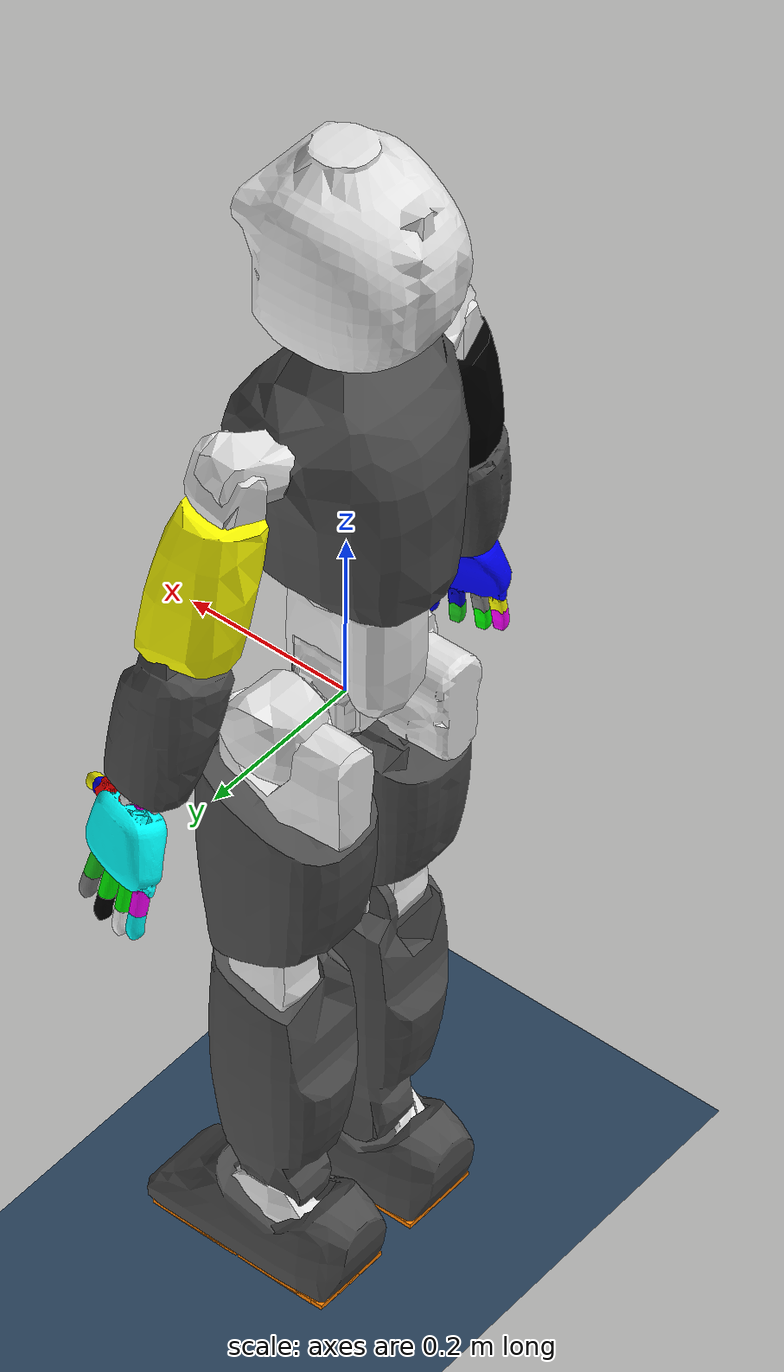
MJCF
<mujoco model="iCub">

  <asset>
    <texture type="skybox" builtin="gradient" rgb1="0.3 0.5 0.7" rgb2="0 0 0" width="512" height="3072" />
    <texture name="plane" type="2d" builtin="checker" rgb1="0.2 0.3 0.4" rgb2="0.1 0.2 0.3" width="128" height="128" mark="cross" markrgb=".8 .8 .8" />
    <material name="plane" reflectance="0.2" texture="plane" texrepeat="5 5" texuniform="true" />
  </asset>

  <visual>
    <headlight diffuse="0.6 0.6 0.6" ambient="0.3 0.3 0.3" specular="0 0 0" />
    <rgba haze="0.15 0.25 0.35 1" />
    <global azimuth="120" elevation="-20" />
  </visual>

  <worldbody>
    <light pos="30 20 10.5" dir="0 0 -1" directional="true" />
    <geom name="floor" type="plane" conaffinity="1" condim="3" contype="1" material="plane" pos="0 0 -0.8" size="0 0 1" />
  </worldbody>

  <option cone="elliptic" impratio="10" />

<compiler angle="radian" meshdir="../robot_descriptions/ergocub-software/urdf/ergoCub/meshes/simmechanics" />
  <statistic meansize="0.0922702" extent="1.66842" center="0.0164501 0.000867736 -0.0627866" />
  <asset>
    <mesh name="sim_ecub_root_link_prt" file="sim_ecub_root_link_prt.stl" scale="0.001 0.001 0.001" />
    <mesh name="sim_ecub_r_hip_1_prt" file="sim_ecub_r_hip_1_prt.stl" scale="0.001 0.001 0.001" />
    <mesh name="sim_ecub_r_hip_2_prt" file="sim_ecub_r_hip_2_prt.stl" scale="0.001 0.001 0.001" />
    <mesh name="sim_ecub_r_hip_3_prt" file="sim_ecub_r_hip_3_prt.stl" scale="0.001 0.001 0.001" />
    <mesh name="sim_ecub_r_upper_leg_prt" file="sim_ecub_r_upper_leg_prt.stl" scale="0.001 0.001 0.001" />
    <mesh name="sim_ecub_r_lower_leg_prt" file="sim_ecub_r_lower_leg_prt.stl" scale="0.001 0.001 0.001" />
    <mesh name="sim_ecub_r_ankle_1_prt" file="sim_ecub_r_ankle_1_prt.stl" scale="0.001 0.001 0.001" />
    <mesh name="sim_ecub_r_ankle_2_prt" file="sim_ecub_r_ankle_2_prt.stl" scale="0.001 0.001 0.001" />
    <mesh name="sim_ecub_r_foot_rear_prt" file="sim_ecub_r_foot_rear_prt.stl" scale="0.001 0.001 0.001" />
    <mesh name="sim_ecub_r_foot_front_prt" file="sim_ecub_r_foot_front_prt.stl" scale="0.001 0.001 0.001" />
    <mesh name="sim_ecub_l_hip_1_prt" file="sim_ecub_l_hip_1_prt.stl" scale="0.001 0.001 0.001" />
    <mesh name="sim_ecub_l_hip_2_prt" file="sim_ecub_l_hip_2_prt.stl" scale="0.001 0.001 0.001" />
    <mesh name="sim_ecub_l_hip_3_prt" file="sim_ecub_l_hip_3_prt.stl" scale="0.001 0.001 0.001" />
    <mesh name="sim_ecub_l_upper_leg_prt" file="sim_ecub_l_upper_leg_prt.stl" scale="0.001 0.001 0.001" />
    <mesh name="sim_ecub_l_lower_leg_prt" file="sim_ecub_l_lower_leg_prt.stl" scale="0.001 0.001 0.001" />
    <mesh name="sim_ecub_l_ankle_1_prt" file="sim_ecub_l_ankle_1_prt.stl" scale="0.001 0.001 0.001" />
    <mesh name="sim_ecub_l_ankle_2_prt" file="sim_ecub_l_ankle_2_prt.stl" scale="0.001 0.001 0.001" />
    <mesh name="sim_ecub_l_foot_front_prt" file="sim_ecub_l_foot_front_prt.stl" scale="0.001 0.001 0.001" />
    <mesh name="sim_ecub_l_foot_rear_prt" file="sim_ecub_l_foot_rear_prt.stl" scale="0.001 0.001 0.001" />
    <mesh name="sim_ecub_torso_1_prt" file="sim_ecub_torso_1_prt.stl" scale="0.001 0.001 0.001" />
    <mesh name="sim_ecub_torso_2_prt" file="sim_ecub_torso_2_prt.stl" scale="0.001 0.001 0.001" />
    <mesh name="sim_ecub_chest_prt" file="sim_ecub_chest_prt.stl" scale="0.001 0.001 0.001" />
    <mesh name="sim_ecub_head_neck_2_prt" file="sim_ecub_head_neck_2_prt.stl" scale="0.001 0.001 0.001" />
    <mesh name="sim_ecub_head_neck_3_prt" file="sim_ecub_head_neck_3_prt.stl" scale="0.001 0.001 0.001" />
    <mesh name="sim_ecub_head_prt" file="sim_ecub_head_prt.stl" scale="0.001 0.001 0.001" />
    <mesh name="sim_ecub_realsense_prt" file="sim_ecub_realsense_prt.stl" scale="0.001 0.001 0.001" />
    <mesh name="sim_ecub_r_shoulder_1_prt" file="sim_ecub_r_shoulder_1_prt.stl" scale="0.001 0.001 0.001" />
    <mesh name="sim_ecub_r_shoulder_2_prt" file="sim_ecub_r_shoulder_2_prt.stl" scale="0.001 0.001 0.001" />
    <mesh name="sim_ecub_r_shoulder_3_prt" file="sim_ecub_r_shoulder_3_prt.stl" scale="0.001 0.001 0.001" />
    <mesh name="sim_ecub_r_upperarm_prt" file="sim_ecub_r_upperarm_prt.stl" scale="0.001 0.001 0.001" />
    <mesh name="sim_ecub_r_forearm_prt" file="sim_ecub_r_forearm_prt.stl" scale="0.001 0.001 0.001" />
    <mesh name="sim_ecub_r_wrist_1_prt" file="sim_ecub_r_wrist_1_prt.stl" scale="0.001 0.001 0.001" />
    <mesh name="sim_ecub_r_wrist_2_prt" file="sim_ecub_r_wrist_2_prt.stl" scale="0.001 0.001 0.001" />
    <mesh name="sim_ecub_r_hand_palm_prt" file="sim_ecub_r_hand_palm_prt.stl" scale="0.001 0.001 0.001" />
    <mesh name="sim_ecub_r_hand_pinkie_1_prt" file="sim_ecub_r_hand_pinkie_1_prt.stl" scale="0.001 0.001 0.001" />
    <mesh name="sim_ecub_r_hand_pinkie_2_prt" file="sim_ecub_r_hand_pinkie_2_prt.stl" scale="0.001 0.001 0.001" />
    <mesh name="sim_ecub_r_hand_thumb_1_prt" file="sim_ecub_r_hand_thumb_1_prt.stl" scale="0.001 0.001 0.001" />
    <mesh name="sim_ecub_r_hand_thumb_2_prt" file="sim_ecub_r_hand_thumb_2_prt.stl" scale="0.001 0.001 0.001" />
    <mesh name="sim_ecub_r_hand_thumb_3_prt" file="sim_ecub_r_hand_thumb_3_prt.stl" scale="0.001 0.001 0.001" />
    <mesh name="sim_ecub_r_hand_middle_1_prt" file="sim_ecub_r_hand_middle_1_prt.stl" scale="0.001 0.001 0.001" />
    <mesh name="sim_ecub_r_hand_middle_2_prt" file="sim_ecub_r_hand_middle_2_prt.stl" scale="0.001 0.001 0.001" />
    <mesh name="sim_ecub_r_hand_ring_1_prt" file="sim_ecub_r_hand_ring_1_prt.stl" scale="0.001 0.001 0.001" />
    <mesh name="sim_ecub_r_hand_ring_2_prt" file="sim_ecub_r_hand_ring_2_prt.stl" scale="0.001 0.001 0.001" />
    <mesh name="sim_ecub_r_hand_index_1_prt" file="sim_ecub_r_hand_index_1_prt.stl" scale="0.001 0.001 0.001" />
    <mesh name="sim_ecub_r_hand_index_2_prt" file="sim_ecub_r_hand_index_2_prt.stl" scale="0.001 0.001 0.001" />
    <mesh name="sim_ecub_r_hand_index_3_prt" file="sim_ecub_r_hand_index_3_prt.stl" scale="0.001 0.001 0.001" />
    <mesh name="sim_ecub_l_shoulder_1_prt" file="sim_ecub_l_shoulder_1_prt.stl" scale="0.001 0.001 0.001" />
    <mesh name="sim_ecub_l_shoulder_2_prt" file="sim_ecub_l_shoulder_2_prt.stl" scale="0.001 0.001 0.001" />
    <mesh name="sim_ecub_l_shoulder_3_prt" file="sim_ecub_l_shoulder_3_prt.stl" scale="0.001 0.001 0.001" />
    <mesh name="sim_ecub_l_upperarm_prt" file="sim_ecub_l_upperarm_prt.stl" scale="0.001 0.001 0.001" />
    <mesh name="sim_ecub_l_forearm_prt" file="sim_ecub_l_forearm_prt.stl" scale="0.001 0.001 0.001" />
    <mesh name="sim_ecub_l_wrist_1_prt" file="sim_ecub_l_wrist_1_prt.stl" scale="0.001 0.001 0.001" />
    <mesh name="sim_ecub_l_wrist_2_prt" file="sim_ecub_l_wrist_2_prt.stl" scale="0.001 0.001 0.001" />
    <mesh name="sim_ecub_l_hand_palm_prt" file="sim_ecub_l_hand_palm_prt.stl" scale="0.001 0.001 0.001" />
    <mesh name="sim_ecub_l_hand_ring_1_prt" file="sim_ecub_l_hand_ring_1_prt.stl" scale="0.001 0.001 0.001" />
    <mesh name="sim_ecub_l_hand_ring_2_prt" file="sim_ecub_l_hand_ring_2_prt.stl" scale="0.001 0.001 0.001" />
    <mesh name="sim_ecub_l_hand_index_1_prt" file="sim_ecub_l_hand_index_1_prt.stl" scale="0.001 0.001 0.001" />
    <mesh name="sim_ecub_l_hand_index_2_prt" file="sim_ecub_l_hand_index_2_prt.stl" scale="0.001 0.001 0.001" />
    <mesh name="sim_ecub_l_hand_index_3_prt" file="sim_ecub_l_hand_index_3_prt.stl" scale="0.001 0.001 0.001" />
    <mesh name="sim_ecub_l_hand_middle_1_prt" file="sim_ecub_l_hand_middle_1_prt.stl" scale="0.001 0.001 0.001" />
    <mesh name="sim_ecub_l_hand_middle_2_prt" file="sim_ecub_l_hand_middle_2_prt.stl" scale="0.001 0.001 0.001" />
    <mesh name="sim_ecub_l_hand_thumb_1_prt" file="sim_ecub_l_hand_thumb_1_prt.stl" scale="0.001 0.001 0.001" />
    <mesh name="sim_ecub_l_hand_thumb_2_prt" file="sim_ecub_l_hand_thumb_2_prt.stl" scale="0.001 0.001 0.001" />
    <mesh name="sim_ecub_l_hand_thumb_3_prt" file="sim_ecub_l_hand_thumb_3_prt.stl" scale="0.001 0.001 0.001" />
    <mesh name="sim_ecub_l_hand_pinkie_1_prt" file="sim_ecub_l_hand_pinkie_1_prt.stl" scale="0.001 0.001 0.001" />
    <mesh name="sim_ecub_l_hand_pinkie_2_prt" file="sim_ecub_l_hand_pinkie_2_prt.stl" scale="0.001 0.001 0.001" />
  </asset>
  <worldbody>
    <body name="root_link">
      <inertial pos="0.0024749 -0.000105079 0.02345" quat="-0.000692861 -0.00578171 -0.00921115 0.999941" mass="2.82375" diaginertia="0.00563092 0.00438033 0.00361615" />
      <joint name="floating_joint" type="free" />
      <geom pos="0 0 0.1785" quat="0.707107 0 0 0.707107" type="mesh" contype="0" conaffinity="0" group="1" density="0" rgba="0.9 0.9 0.9 1" mesh="sim_ecub_root_link_prt" />
      <geom pos="0 0 0.1785" quat="0.707107 0 0 0.707107" type="mesh" rgba="0.9 0.9 0.9 1" mesh="sim_ecub_root_link_prt" />
      <body name="r_hip_1" pos="0.0211 -0.0505 0">
        <inertial pos="-0.0040321 -0.0282494 -0.000674" quat="0.471583 0.463949 0.507259 0.552313" mass="2.23209" diaginertia="0.00270348 0.00246138 0.00220385" />
        <joint name="r_hip_pitch" pos="0 0 0" axis="0 -1 0" range="-0.750492 1.79769" damping="50" />
        <geom pos="-0.0211 0.0505 0.1785" quat="0.707107 0 0 0.707107" type="mesh" contype="0" conaffinity="0" group="1" density="0" rgba="0.9 0.9 0.9 1" mesh="sim_ecub_r_hip_1_prt" />
        <geom pos="-0.0211 0.0505 0.1785" quat="0.707107 0 0 0.707107" type="mesh" rgba="0.9 0.9 0.9 1" mesh="sim_ecub_r_hip_1_prt" />
        <body name="r_hip_2" pos="-0.04725 -0.0331 -0.009">
          <inertial pos="0.0206737 0.00690112 -0.0935168" quat="0.685131 -0.126138 -0.177679 0.695065" mass="3.9815" diaginertia="0.02644 0.0237871 0.00862537" />
          <joint name="r_hip_roll" pos="0 0 0" axis="-1 0 0" range="-0.279253 1.90241" damping="50" />
          <geom pos="0.0262 0.0836 0.1875" quat="0.707107 0 0 0.707107" type="mesh" contype="0" conaffinity="0" group="1" density="0" rgba="0.9 0.9 0.9 1" mesh="sim_ecub_r_hip_2_prt" />
          <geom pos="0.0262 0.0836 0.1875" quat="0.707107 0 0 0.707107" type="mesh" rgba="0.9 0.9 0.9 1" mesh="sim_ecub_r_hip_2_prt" />
          <geom pos="0.0262 0.0836 0.1875" quat="0.707107 0 0 0.707107" type="mesh" contype="0" conaffinity="0" group="1" density="0" rgba="0.3 0.3 0.3 1" mesh="sim_ecub_r_hip_3_prt" />
          <geom pos="0.0262 0.0836 0.1875" quat="0.707107 0 0 0.707107" type="mesh" rgba="0.3 0.3 0.3 1" mesh="sim_ecub_r_hip_3_prt" />
          <body name="r_upper_leg" pos="0.0367 0.015 -0.1624" quat="1 0 0 5.9369e-07">
            <inertial pos="0.00851748 -0.0144685 -0.12675" quat="0.752216 -0.0338778 -0.00759657 0.658001" mass="2.78492" diaginertia="0.0121302 0.0118863 0.00221412" />
            <joint name="r_hip_yaw" pos="0 0 0" axis="0 0 -1" range="-1.37881 1.37881" damping="50" />
            <geom pos="-0.0105 0.0686 0.3499" quat="0.707107 0 0 0.707107" type="mesh" contype="0" conaffinity="0" group="1" density="0" rgba="0.9 0.9 0.9 1" mesh="sim_ecub_r_upper_leg_prt" />
            <geom pos="-0.0105 0.0686 0.3499" quat="0.707107 0 0 0.707107" type="mesh" rgba="0.9 0.9 0.9 1" mesh="sim_ecub_r_upper_leg_prt" />
            <body name="r_lower_leg" pos="0.0106 0.00789999 -0.1797" quat="0 1 -5.9369e-07 0">
              <inertial pos="0.0011585 0.0062002 0.214259" quat="0.00842304 0.725858 -0.687437 0.0221305" mass="3.74161" diaginertia="0.0473358 0.0460276 0.00468999" />
              <joint name="r_knee" pos="0 0 0" axis="0 1 0" range="-1.81514 0.10472" damping="50" />
              <geom pos="-0.0211 -0.0607 -0.5296" quat="0 0.707107 -0.707107 0" type="mesh" contype="0" conaffinity="0" group="1" density="0" rgba="0.3 0.3 0.3 1" mesh="sim_ecub_r_lower_leg_prt" />
              <geom pos="-0.0211 -0.0607 -0.5296" quat="0 0.707107 -0.707107 0" type="mesh" rgba="0.3 0.3 0.3 1" mesh="sim_ecub_r_lower_leg_prt" />
              <body name="r_ankle_1" pos="0 0.0319 0.321" quat="0 1 0 0">
                <inertial pos="-0.0013672 -0.0006602 -0.014087" quat="-0.341324 0.612062 0.685794 0.196378" mass="0.348128" diaginertia="0.0100553 0.0100032 0.00994156" />
                <joint name="r_ankle_pitch" pos="0 0 0" axis="0 1 0" range="-0.785398 0.785398" damping="50" />
                <geom pos="-0.0211 0.0926 0.8506" quat="0.707107 0 0 0.707107" type="mesh" contype="0" conaffinity="0" group="1" density="0" rgba="0.9 0.9 0.9 1" mesh="sim_ecub_r_ankle_1_prt" />
                <geom pos="-0.0211 0.0926 0.8506" quat="0.707107 0 0 0.707107" type="mesh" rgba="0.9 0.9 0.9 1" mesh="sim_ecub_r_ankle_1_prt" />
                <body name="r_ankle_2" pos="-0.05275 0.0182 -0.035">
                  <inertial pos="0.0484804 -6.71428e-05 -0.0336846" quat="0.000552937 0.88728 -0.0103566 0.461115" mass="1.98403" diaginertia="0.033318 0.0326761 0.0293578" />
                  <joint name="r_ankle_roll" pos="0 0 0" axis="-1 0 0" range="-0.436332 0.436332" damping="50" />
                  <geom pos="0.03165 0.0744 0.8856" quat="0.707107 0 0 0.707107" type="mesh" contype="0" conaffinity="0" group="1" density="0" rgba="0.3 0.3 0.3 1" mesh="sim_ecub_r_ankle_2_prt" />
                  <geom pos="0.03165 0.0744 0.8856" quat="0.707107 0 0 0.707107" type="mesh" rgba="0.3 0.3 0.3 1" mesh="sim_ecub_r_ankle_2_prt" />
                  <geom pos="0.0316 0.0744 0.8856" quat="0.707107 0 0 0.707107" type="mesh" contype="0" conaffinity="0" group="1" density="0" rgba="1 0.51 0 1" mesh="sim_ecub_r_foot_rear_prt" />
                  <geom size="0.0585 0.05 0.003" pos="0.016 0 -0.0672" type="box" rgba="1 0.51 0 1" />
                  <geom pos="0.03165 0.0744 0.8856" quat="0.707107 0 0 0.707107" type="mesh" contype="0" conaffinity="0" group="1" density="0" rgba="1 0.51 0 1" mesh="sim_ecub_r_foot_front_prt" />
                  <geom size="0.0585 0.05 0.003" pos="0.13525 0 -0.0672" type="box" rgba="1 0.51 0 1" />
                </body>
              </body>
            </body>
          </body>
        </body>
      </body>
      <body name="l_hip_1" pos="0.0211 0.0505 0">
        <inertial pos="-0.0040154 0.0282473 -0.000681" quat="0.551419 0.506606 0.463763 0.473509" mass="2.23177" diaginertia="0.00270283 0.00246163 0.00220285" />
        <joint name="l_hip_pitch" pos="0 0 0" axis="0 -1 0" range="-0.750492 1.79769" damping="50" />
        <geom pos="-0.0211 -0.0505 0.1785" quat="0.707107 0 0 0.707107" type="mesh" contype="0" conaffinity="0" group="1" density="0" rgba="0.9 0.9 0.9 1" mesh="sim_ecub_l_hip_1_prt" />
        <geom pos="-0.0211 -0.0505 0.1785" quat="0.707107 0 0 0.707107" type="mesh" rgba="0.9 0.9 0.9 1" mesh="sim_ecub_l_hip_1_prt" />
        <body name="l_hip_2" pos="-0.04725 0.0331 -0.009">
          <inertial pos="0.0206874 -0.00690172 -0.0935735" quat="0.69574 -0.176627 -0.125492 0.684836" mass="3.98136" diaginertia="0.0265634 0.0238959 0.00864075" />
          <joint name="l_hip_roll" pos="0 0 0" axis="1 0 0" range="-0.279253 1.90241" damping="50" />
          <geom pos="0.02615 -0.0836 0.1875" quat="0.707107 0 0 0.707107" type="mesh" contype="0" conaffinity="0" group="1" density="0" rgba="0.9 0.9 0.9 1" mesh="sim_ecub_l_hip_2_prt" />
          <geom pos="0.02615 -0.0836 0.1875" quat="0.707107 0 0 0.707107" type="mesh" rgba="0.9 0.9 0.9 1" mesh="sim_ecub_l_hip_2_prt" />
          <geom pos="0.02615 -0.0836 0.1875" quat="0.707107 0 0 0.707107" type="mesh" contype="0" conaffinity="0" group="1" density="0" rgba="0.3 0.3 0.3 1" mesh="sim_ecub_l_hip_3_prt" />
          <geom pos="0.02615 -0.0836 0.1875" quat="0.707107 0 0 0.707107" type="mesh" rgba="0.3 0.3 0.3 1" mesh="sim_ecub_l_hip_3_prt" />
          <body name="l_upper_leg" pos="0.0367 -0.015 -0.1624">
            <inertial pos="0.0085035 0.0144849 -0.126747" quat="0.666541 -0.00759957 -0.0335156 0.744676" mass="2.78492" diaginertia="0.0121286 0.0118796 0.00220771" />
            <joint name="l_hip_yaw" pos="0 0 0" axis="0 0 1" range="-1.37881 1.37881" damping="50" />
            <geom pos="-0.01055 -0.0686 0.3499" quat="0.707107 0 0 0.707107" type="mesh" contype="0" conaffinity="0" group="1" density="0" rgba="0.9 0.9 0.9 1" mesh="sim_ecub_l_upper_leg_prt" />
            <geom pos="-0.01055 -0.0686 0.3499" quat="0.707107 0 0 0.707107" type="mesh" rgba="0.9 0.9 0.9 1" mesh="sim_ecub_l_upper_leg_prt" />
            <body name="l_lower_leg" pos="0.0106 -0.0079 -0.1797" quat="0 1 0 0">
              <inertial pos="0.0013845 -0.0061871 0.21426" quat="-0.0218229 0.692096 -0.721423 -0.00870268" mass="3.74161" diaginertia="0.0473316 0.0460262 0.00468891" />
              <joint name="l_knee" pos="0 0 0" axis="0 1 0" range="-1.81514 0.10472" damping="50" />
              <geom pos="-0.02115 0.0607 -0.5296" quat="0 0.707107 -0.707107 0" type="mesh" contype="0" conaffinity="0" group="1" density="0" rgba="0.3 0.3 0.3 1" mesh="sim_ecub_l_lower_leg_prt" />
              <geom pos="-0.02115 0.0607 -0.5296" quat="0 0.707107 -0.707107 0" type="mesh" rgba="0.3 0.3 0.3 1" mesh="sim_ecub_l_lower_leg_prt" />
              <body name="l_ankle_1" pos="0 -0.0319 0.321" quat="0 1 0 0">
                <inertial pos="-0.0013852 0.0006602 -0.014087" quat="0.672931 -0.201319 0.337043 0.626927" mass="0.348128" diaginertia="0.0100553 0.0100024 0.00994233" />
                <joint name="l_ankle_pitch" pos="0 0 0" axis="0 1 0" range="-0.785398 0.785398" damping="50" />
                <geom pos="-0.02115 -0.0926 0.8506" quat="0.707107 0 0 0.707107" type="mesh" contype="0" conaffinity="0" group="1" density="0" rgba="0.9 0.9 0.9 1" mesh="sim_ecub_l_ankle_1_prt" />
                <geom pos="-0.02115 -0.0926 0.8506" quat="0.707107 0 0 0.707107" type="mesh" rgba="0.9 0.9 0.9 1" mesh="sim_ecub_l_ankle_1_prt" />
                <body name="l_ankle_2" pos="-0.05275 -0.0182 -0.035">
                  <inertial pos="0.0484773 -7.60796e-05 -0.0336846" quat="0.00298131 0.887389 -0.00182841 0.461008" mass="1.98403" diaginertia="0.0333205 0.0326762 0.0293554" />
                  <joint name="l_ankle_roll" pos="0 0 0" axis="1 0 0" range="-0.436332 0.436332" damping="50" />
                  <geom pos="0.0316 -0.0744 0.8856" quat="0.707107 0 0 0.707107" type="mesh" contype="0" conaffinity="0" group="1" density="0" rgba="0.3 0.3 0.3 1" mesh="sim_ecub_l_ankle_2_prt" />
                  <geom pos="0.0316 -0.0744 0.8856" quat="0.707107 0 0 0.707107" type="mesh" rgba="0.3 0.3 0.3 1" mesh="sim_ecub_l_ankle_2_prt" />
                  <geom pos="0.0316 -0.0744 0.8856" quat="0.707107 0 0 0.707107" type="mesh" contype="0" conaffinity="0" group="1" density="0" rgba="1 0.51 0 1" mesh="sim_ecub_l_foot_front_prt" />
                  <geom size="0.0585 0.05 0.003" pos="0.13525 0 -0.0672" type="box" rgba="1 0.51 0 1" />
                  <geom pos="0.0316 -0.0744 0.8856" quat="0.707107 0 0 0.707107" type="mesh" contype="0" conaffinity="0" group="1" density="0" rgba="1 0.51 0 1" mesh="sim_ecub_l_foot_rear_prt" />
                  <geom size="0.0585 0.05 0.003" pos="0.016 0 -0.0672" type="box" rgba="1 0.51 0 1" />
                </body>
              </body>
            </body>
          </body>
        </body>
      </body>
      <body name="torso_1" pos="0 0 0.0605">
        <inertial pos="-0.00963997 0.00061685 0.0824423" quat="0.700604 0.0855404 0.0875458 0.702974" mass="2.06457" diaginertia="0.00740614 0.00613235 0.00299268" />
        <joint name="torso_roll" pos="0 0 0" axis="-1 0 0" range="-0.401426 0.401426" damping="50" />
        <geom pos="0 0 0.118" quat="0.707107 0 0 0.707107" type="mesh" contype="0" conaffinity="0" group="1" density="0" rgba="0.9 0.9 0.9 1" mesh="sim_ecub_torso_1_prt" />
        <geom pos="0 0 0.118" quat="0.707107 0 0 0.707107" type="mesh" rgba="0.9 0.9 0.9 1" mesh="sim_ecub_torso_1_prt" />
        <body name="torso_2" pos="0 0 0.118">
          <inertial pos="0.00157247 0.00362235 0.0260195" quat="-0.0181108 0.0146525 0.755585 0.654636" mass="0.705163" diaginertia="0.00125929 0.00115568 0.000657438" />
          <joint name="torso_pitch" pos="0 0 0" axis="0 1 0" range="-0.314159 0.785398" damping="50" />
          <geom quat="0.707107 0 0 0.707107" type="mesh" contype="0" conaffinity="0" group="1" density="0" rgba="0.9 0.9 0.9 1" mesh="sim_ecub_torso_2_prt" />
          <geom quat="0.707107 0 0 0.707107" type="mesh" rgba="0.9 0.9 0.9 1" mesh="sim_ecub_torso_2_prt" />
          <body name="chest" pos="0 0 0.06447">
            <inertial pos="-0.010721 -0.000348206 0.076111" quat="-0.0252821 0.00885239 0.00421446 0.999632" mass="8.06547" diaginertia="0.0484694 0.044931 0.0306811" />
            <joint name="torso_yaw" pos="0 0 0" axis="0 0 -1" range="-0.750492 0.750492" damping="50" />
            <geom pos="0 0 -0.06447" quat="0.707107 0 0 0.707107" type="mesh" contype="0" conaffinity="0" group="1" density="0" rgba="0.3 0.3 0.3 1" mesh="sim_ecub_chest_prt" />
            <geom pos="0 0 -0.06447" quat="0.707107 0 0 0.707107" type="mesh" rgba="0.3 0.3 0.3 1" mesh="sim_ecub_chest_prt" />
            <body name="neck_2" pos="0.00486151 0 0.2253">
              <inertial pos="-0.00630577 3.01413e-05 0.006373" quat="3.55339e-05 -0.281959 -0.00735769 0.959398" mass="0.121003" diaginertia="5.09387e-05 3.84906e-05 3.19869e-05" />
              <joint name="neck_pitch" pos="0 0 0" axis="0 -1 0" range="-0.523599 0.383972" damping="50" />
              <geom pos="-0.00486151 -5e-05 -0.28977" quat="0.707107 0 0 0.707107" type="mesh" contype="0" conaffinity="0" group="1" density="0" rgba="0.9 0.9 0.9 1" mesh="sim_ecub_head_neck_2_prt" />
              <geom pos="-0.00486151 -5e-05 -0.28977" quat="0.707107 0 0 0.707107" type="mesh" rgba="0.9 0.9 0.9 1" mesh="sim_ecub_head_neck_2_prt" />
              <body name="neck_3" pos="0 0 0.0095">
                <inertial pos="0.00075905 -4.09169e-05 0.036035" quat="0.711625 -0.0362238 -0.034139 0.700794" mass="0.178114" diaginertia="0.000107601 9.76645e-05 3.56511e-05" />
                <joint name="neck_roll" pos="0 0 0" axis="1 0 0" range="-0.349066 0.349066" damping="50" />
                <geom pos="-0.00486151 0 -0.29927" quat="0.707107 0 0 0.707107" type="mesh" contype="0" conaffinity="0" group="1" density="0" rgba="0.9 0.9 0.9 1" mesh="sim_ecub_head_neck_3_prt" />
                <geom pos="-0.00486151 0 -0.29927" quat="0.707107 0 0 0.707107" type="mesh" rgba="0.9 0.9 0.9 1" mesh="sim_ecub_head_neck_3_prt" />
                <body name="head" pos="0 0 0.06915">
                  <inertial pos="-0.0203885 0.0040021 0.034332" quat="0.727423 0.230215 0.158946 0.626573" mass="2.31933" diaginertia="0.0122781 0.0106049 0.0100972" />
                  <joint name="neck_yaw" pos="0 0 0" axis="0 0 1" range="-0.785398 0.785398" damping="50" />
                  <geom pos="-0.00486151 0 -0.36842" quat="0.707107 0 0 0.707107" type="mesh" contype="0" conaffinity="0" group="1" density="0" rgba="0.9 0.9 0.9 1" mesh="sim_ecub_head_prt" />
                  <geom pos="-0.00486151 0 -0.36842" quat="0.707107 0 0 0.707107" type="mesh" rgba="0.9 0.9 0.9 1" mesh="sim_ecub_head_prt" />
                  <body name="realsense" pos="0.06251 -3e-05 0.076393" quat="1 0 0.000129791 0">
                    <inertial pos="-0.0156655 0.00452 0.00274493" quat="0.469029 0.801177 0.221584 0.298376" mass="0.0973042" diaginertia="0.0100515 0.0100059 0.00994255" />
                    <joint name="camera_tilt" pos="0 0 0" axis="0 -1 0" range="-0.523599 0.523599" damping="50" />
                    <geom pos="-0.067256 3e-05 -0.44483" quat="0.707107 -9.17761e-05 -9.17761e-05 0.707107" type="mesh" contype="0" conaffinity="0" group="1" density="0" rgba="0 1 0 1" mesh="sim_ecub_realsense_prt" />
                    <geom pos="-0.067256 3e-05 -0.44483" quat="0.707107 -9.17761e-05 -9.17761e-05 0.707107" type="mesh" rgba="0 1 0 1" mesh="sim_ecub_realsense_prt" />
                  </body>
                </body>
              </body>
            </body>
            <body name="r_shoulder_1" pos="-0.0135187 -0.0670476 0.12352" quat="0.982708 -0.121688 -0.0429061 0.132799">
              <inertial pos="0.000172398 -0.0678405 0.000475572" quat="0.703279 0.596364 -0.0710268 0.3804" mass="0.792282" diaginertia="0.010259 0.0100497 0.00969132" />
              <joint name="r_shoulder_pitch" pos="0 0 0" axis="-3.35225e-07 1 -2.20686e-07" range="-2.96706 0.610865" damping="50" />
              <geom pos="0.0214149 0.106413 -0.168036" quat="0.788783 0.116385 -0.055707 0.600977" type="mesh" contype="0" conaffinity="0" group="1" density="0" rgba="0.9 0.9 0.9 1" mesh="sim_ecub_r_shoulder_1_prt" />
              <geom pos="0.0214149 0.106413 -0.168036" quat="0.788783 0.116385 -0.055707 0.600977" type="mesh" rgba="0.9 0.9 0.9 1" mesh="sim_ecub_r_shoulder_1_prt" />
              <body name="r_shoulder_2" pos="0.00749996 -0.0933001 -6.00683e-07">
                <inertial pos="0.000512067 -0.000143644 -0.0364077" quat="0.902256 -0.118407 0.222249 -0.350028" mass="0.710693" diaginertia="0.0203685 0.0203499 0.0199177" />
                <joint name="r_shoulder_roll" pos="0 0 0" axis="-1 1.71286e-07 2.92871e-07" range="-0.261799 2.61799" damping="50" />
                <geom pos="0.0139014 0.199666 -0.168047" quat="0.788783 0.116385 -0.055707 0.600977" type="mesh" contype="0" conaffinity="0" group="1" density="0" rgba="0.9 0.9 0.9 1" mesh="sim_ecub_r_shoulder_2_prt" />
                <geom pos="0.0139014 0.199666 -0.168047" quat="0.788783 0.116385 -0.055707 0.600977" type="mesh" rgba="0.9 0.9 0.9 1" mesh="sim_ecub_r_shoulder_2_prt" />
                <geom pos="0.0139014 0.199666 -0.168047" quat="0.788783 0.116385 -0.055707 0.600977" type="mesh" contype="0" conaffinity="0" group="1" density="0" rgba="0.9 0.9 0.9 1" mesh="sim_ecub_r_shoulder_3_prt" />
                <geom pos="0.0139014 0.199666 -0.168047" quat="0.788783 0.116385 -0.055707 0.600977" type="mesh" rgba="0.9 0.9 0.9 1" mesh="sim_ecub_r_shoulder_3_prt" />
                <body name="r_upper_arm" pos="-0.00684991 3.26793e-07 -0.0767999">
                  <inertial pos="0.000147064 -0.00233532 -0.0501167" quat="0.797511 -0.0270149 0.0111229 0.602596" mass="1.77224" diaginertia="0.00352538 0.00341395 0.00156994" />
                  <joint name="r_shoulder_yaw" pos="0 0 0" axis="1.71338e-07 -2.36593e-07 1" range="-0.872665 1.39626" damping="50" />
                  <geom pos="0.0207514 0.199666 -0.0912466" quat="0.788783 0.116385 -0.055707 0.600977" type="mesh" contype="0" conaffinity="0" group="1" density="0" rgba="0 0 0 1" mesh="sim_ecub_r_upperarm_prt" />
                  <geom pos="0.0207514 0.199666 -0.0912466" quat="0.788783 0.116385 -0.055707 0.600977" type="mesh" rgba="0 0 0 1" mesh="sim_ecub_r_upperarm_prt" />
                  <body name="r_forearm" pos="0.01 0.00150007 -0.1237">
                    <inertial pos="-0.0183071 -0.0022154 -0.0881495" quat="0.646973 -0.201237 0.172893 0.714869" mass="1.47607" diaginertia="0.010598 0.0100223 0.00937974" />
                    <joint name="r_elbow" pos="0 0 0" axis="3.35225e-07 -1 2.20686e-07" range="-0.0523599 1.309" damping="50" />
                    <geom pos="0.0107513 0.198166 0.032453" quat="0.788783 0.116385 -0.055707 0.600977" type="mesh" contype="0" conaffinity="0" group="1" density="0" rgba="0.3 0.3 0.3 1" mesh="sim_ecub_r_forearm_prt" />
                    <geom pos="0.0107513 0.198166 0.032453" quat="0.788783 0.116385 -0.055707 0.600977" type="mesh" rgba="0.3 0.3 0.3 1" mesh="sim_ecub_r_forearm_prt" />
                    <body name="r_wrist_1" pos="-0.0150002 -0.00200069 -0.19435">
                      <inertial pos="0.000402763 -0.00105883 0.0191411" quat="0.621183 0.061885 0.373481 0.686159" mass="0.0565425" diaginertia="0.010002 0.00999986 0.00999809" />
                      <joint name="r_wrist_yaw" pos="0 0 0" axis="1.71338e-07 -2.36593e-07 1" range="-1.6057 1.6057" damping="50" />
                      <geom pos="0.0257515 0.200167 0.226803" quat="0.788783 0.116385 -0.055707 0.600977" type="mesh" contype="0" conaffinity="0" group="1" density="0" rgba="0.9 0.9 0.9 1" mesh="sim_ecub_r_wrist_1_prt" />
                      <geom pos="0.0257515 0.200167 0.226803" quat="0.788783 0.116385 -0.055707 0.600977" type="mesh" rgba="0.9 0.9 0.9 1" mesh="sim_ecub_r_wrist_1_prt" />
                      <body name="r_wrist_2">
                        <inertial pos="0.00392272 -0.0045195 0.0122774" quat="0.524878 -0.255071 0.117868 0.80346" mass="0.0264562" diaginertia="0.0100189 0.0100025 0.0099786" />
                        <joint name="r_wrist_roll" pos="0 0 0" axis="1 -1.71286e-07 -2.92871e-07" range="-1.0821 0.907571" damping="50" />
                        <geom pos="0.0257515 0.200167 0.226803" quat="0.788783 0.116385 -0.055707 0.600977" type="mesh" contype="0" conaffinity="0" group="1" density="0" rgba="1 0 0 1" mesh="sim_ecub_r_wrist_2_prt" />
                        <geom pos="0.0257515 0.200167 0.226803" quat="0.788783 0.116385 -0.055707 0.600977" type="mesh" rgba="1 0 0 1" mesh="sim_ecub_r_wrist_2_prt" />
                        <body name="r_hand_palm">
                          <inertial pos="-0.00386798 -0.0027925 -0.0597035" quat="0.639353 0.118309 0.396436 0.648128" mass="0.189135" diaginertia="0.0100227 0.0100052 0.0099721" />
                          <joint name="r_wrist_pitch" pos="0 0 0" axis="3.35225e-07 -1 2.20686e-07" range="-0.558505 0.558505" damping="50" />
                          <geom pos="0.0257515 0.200167 0.226803" quat="0.788783 0.116385 -0.055707 0.600977" type="mesh" contype="0" conaffinity="0" group="1" density="0" rgba="0 0 1 1" mesh="sim_ecub_r_hand_palm_prt" />
                          <geom pos="0.0257515 0.200167 0.226803" quat="0.788783 0.116385 -0.055707 0.600977" type="mesh" rgba="0 0 1 1" mesh="sim_ecub_r_hand_palm_prt" />
                          <body name="r_hand_pinkie_1" pos="-0.0359823 0.00238868 -0.0920853" quat="0.013077 0.043616 -0.000570957 0.998963">
                            <inertial pos="0.000120667 0.00370525 -0.0119666" quat="0.655105 0.187387 0.185267 -0.708096" mass="0.00283627" diaginertia="0.01 0.01 0.00999997" />
                            <joint name="r_pinkie_prox" pos="0 0 0" axis="-1 1.97921e-07 4.06013e-07" range="0 1.5708" damping="50" />
                            <geom pos="-0.0285272 -0.199326 0.322602" quat="0.615776 -0.0881877 -0.0903306 -0.777742" type="mesh" contype="0" conaffinity="0" group="1" density="0" rgba="1 1 0 1" mesh="sim_ecub_r_hand_pinkie_1_prt" />
                            <geom pos="-0.0285272 -0.199326 0.322602" quat="0.615776 -0.0881877 -0.0903306 -0.777742" type="mesh" rgba="1 1 0 1" mesh="sim_ecub_r_hand_pinkie_1_prt" />
                            <body name="r_hand_pinkie_2" pos="0 -0.00149975 -0.0250002">
                              <inertial pos="1.71971e-05 0.00178469 -0.00561191" quat="0.64317 0.179539 0.195709 -0.71819" mass="0.00857923" diaginertia="0.0100007 0.01 0.00999926" />
                              <joint name="r_pinkie_dist" pos="0 0 0" axis="-1 1.97921e-07 4.06013e-07" range="0 1.62839" damping="50" />
                              <geom pos="-0.0285273 -0.197827 0.347603" quat="0.615776 -0.0881877 -0.0903306 -0.777742" type="mesh" contype="0" conaffinity="0" group="1" density="0" rgba="1 0 1 1" mesh="sim_ecub_r_hand_pinkie_2_prt" />
                              <geom pos="-0.0285273 -0.197827 0.347603" quat="0.615776 -0.0881877 -0.0903306 -0.777742" type="mesh" rgba="1 0 1 1" mesh="sim_ecub_r_hand_pinkie_2_prt" />
                            </body>
                          </body>
                          <body name="r_hand_thumb_1" pos="0.0233749 0.00300008 -0.0345235" quat="0.974289 -0.022194 -0.111006 0.194796">
                            <inertial pos="0.0207581 -0.0027448 -0.00880548" quat="0.487224 -0.298466 -0.293487 0.766418" mass="0.0346205" diaginertia="0.010003 0.0100006 0.00999636" />
                            <joint name="r_thumb_add" pos="0 0 0" axis="9.57907e-08 6.90101e-08 1" range="0 1.5708" damping="50" />
                            <geom pos="0.132215 0.158516 0.254094" quat="0.889171 0.18676 -0.00272445 0.417718" type="mesh" contype="0" conaffinity="0" group="1" density="0" rgba="0 1 1 1" mesh="sim_ecub_r_hand_thumb_1_prt" />
                            <geom pos="0.132215 0.158516 0.254094" quat="0.889171 0.18676 -0.00272445 0.417718" type="mesh" rgba="0 1 1 1" mesh="sim_ecub_r_hand_thumb_1_prt" />
                            <body name="r_hand_thumb_2" pos="0.0345419 -0.0031448 -0.0260718" quat="0.591557 0.740051 0.199788 -0.24994">
                              <inertial pos="0.00979188 0.00433944 0.000262676" quat="-0.339637 -0.510436 0.389894 0.687084" mass="0.00246082" diaginertia="0.01 0.01 0.00999996" />
                              <joint name="r_thumb_prox" pos="0 0 0" axis="2.0368e-07 1.50085e-07 -1" range="0 1.43292" damping="50" />
                              <geom pos="-0.0921942 0.239476 -0.219815" quat="0.559259 -0.630327 0.176553 0.508672" type="mesh" contype="0" conaffinity="0" group="1" density="0" rgba="0 1 0 1" mesh="sim_ecub_r_hand_thumb_2_prt" />
                              <geom pos="-0.0921942 0.239476 -0.219815" quat="0.559259 -0.630327 0.176553 0.508672" type="mesh" rgba="0 1 0 1" mesh="sim_ecub_r_hand_thumb_2_prt" />
                              <body name="r_hand_thumb_3" pos="0.0199995 -0.00149952 -3.90935e-07">
                                <inertial pos="0.00646418 0.0018849 1.54041e-05" quat="0.60754 -0.146366 0.76223 -0.168754" mass="0.00811336" diaginertia="0.0100008 0.0100003 0.0099989" />
                                <joint name="r_thumb_dist" pos="0 0 0" axis="2.0368e-07 1.50085e-07 -1" range="0 0.935496" damping="50" />
                                <geom pos="-0.112194 0.240976 -0.219814" quat="0.559259 -0.630327 0.176553 0.508672" type="mesh" contype="0" conaffinity="0" group="1" density="0" rgba="1 1 1 1" mesh="sim_ecub_r_hand_thumb_3_prt" />
                                <geom pos="-0.112194 0.240976 -0.219814" quat="0.559259 -0.630327 0.176553 0.508672" type="mesh" rgba="1 1 1 1" mesh="sim_ecub_r_hand_thumb_3_prt" />
                              </body>
                            </body>
                          </body>
                          <body name="r_hand_middle_1" pos="0.00960016 0.00150086 -0.103" quat="9.28173e-08 -2.82515e-07 0 -1">
                            <inertial pos="0.000142889 0.00364327 -0.0143316" quat="0.765199 0.138116 0.234811 -0.583317" mass="0.00345703" diaginertia="0.0100001 0.01 0.00999994" />
                            <joint name="r_middle_prox" pos="0 0 0" axis="-1 3.5692e-07 2.72158e-07" range="0 1.5708" damping="50" />
                            <geom pos="-0.0161512 -0.198666 0.329803" quat="0.600977 -0.0557072 -0.116385 -0.788783" type="mesh" contype="0" conaffinity="0" group="1" density="0" rgba="0 0 0.8 1" mesh="sim_ecub_r_hand_middle_1_prt" />
                            <geom pos="-0.0161512 -0.198666 0.329803" quat="0.600977 -0.0557072 -0.116385 -0.788783" type="mesh" rgba="0 0 0.8 1" mesh="sim_ecub_r_hand_middle_1_prt" />
                            <body name="r_hand_middle_2" pos="1.35502e-07 -0.00149952 -0.0300002" quat="1 -0.000936086 1.206e-10 -1.28834e-07">
                              <inertial pos="5.14311e-05 0.00159948 -0.0035911" quat="0.7185 0.153544 0.22765 -0.639028" mass="0.00912524" diaginertia="0.0100009 0.0100001 0.00999899" />
                              <joint name="r_middle_dist" pos="0 0 0" axis="-1 9.87832e-08 2.50448e-07" range="0 1.73137" damping="50" />
                              <geom pos="-0.0161513 -0.19784 0.359433" quat="0.601029 -0.0551446 -0.115647 -0.788891" type="mesh" contype="0" conaffinity="0" group="1" density="0" rgba="0.1 0.8 0.1 1" mesh="sim_ecub_r_hand_middle_2_prt" />
                              <geom pos="-0.0161513 -0.19784 0.359433" quat="0.601029 -0.0551446 -0.115647 -0.788891" type="mesh" rgba="0.1 0.8 0.1 1" mesh="sim_ecub_r_hand_middle_2_prt" />
                            </body>
                          </body>
                          <body name="r_hand_ring_1" pos="-0.0154179 0.0018501 -0.0979004" quat="0.013077 0.043616 -0.000570957 0.998963">
                            <inertial pos="0.000142554 0.00364206 -0.0143318" quat="0.660046 0.17656 0.198198 -0.702769" mass="0.00345703" diaginertia="0.0100001 0.01 0.00999994" />
                            <joint name="r_ring_prox" pos="0 0 0" axis="-1 1.97921e-07 4.06013e-07" range="0 1.5708" damping="50" />
                            <geom pos="-0.00752724 -0.199326 0.326602" quat="0.615776 -0.0881877 -0.0903306 -0.777742" type="mesh" contype="0" conaffinity="0" group="1" density="0" mesh="sim_ecub_r_hand_ring_1_prt" />
                            <geom pos="-0.00752724 -0.199326 0.326602" quat="0.615776 -0.0881877 -0.0903306 -0.777742" type="mesh" mesh="sim_ecub_r_hand_ring_1_prt" />
                            <body name="r_hand_ring_2" pos="0 -0.00149992 -0.0300006">
                              <inertial pos="5.12902e-05 0.00166963 -0.00359381" quat="0.643807 0.177623 0.198011 -0.717464" mass="0.0091955" diaginertia="0.0100009 0.01 0.00999904" />
                              <joint name="r_ring_dist" pos="0 0 0" axis="-1 1.97921e-07 4.06013e-07" range="0 1.73137" damping="50" />
                              <geom pos="-0.00752719 -0.197826 0.356603" quat="0.615776 -0.0881877 -0.0903306 -0.777742" type="mesh" contype="0" conaffinity="0" group="1" density="0" rgba="0 1 0 1" mesh="sim_ecub_r_hand_ring_2_prt" />
                              <geom pos="-0.00752719 -0.197826 0.356603" quat="0.615776 -0.0881877 -0.0903306 -0.777742" type="mesh" rgba="0 1 0 1" mesh="sim_ecub_r_hand_ring_2_prt" />
                            </body>
                          </body>
                          <body name="r_hand_index_1" pos="0.0224701 0.00150063 -0.0685895" quat="2.31007e-08 -0.0436192 1.00859e-09 0.999048">
                            <inertial pos="-0.00875698 0.0041775 -0.0177834" quat="0.941965 0.0557443 0.276084 -0.18268" mass="0.0183891" diaginertia="0.0100005 0.01 0.00999949" />
                            <joint name="r_index_add" pos="0 0 0" axis="-3.99252e-07 1 2.1442e-07" range="0 0.261799" damping="50" />
                            <geom pos="-0.0290139 -0.198666 0.293983" quat="0.595328 -0.021248 -0.142489 -0.790462" type="mesh" contype="0" conaffinity="0" group="1" density="0" rgba="0 0 0 1" mesh="sim_ecub_r_hand_index_1_prt" />
                            <geom pos="-0.0290139 -0.198666 0.293983" quat="0.595328 -0.021248 -0.142489 -0.790462" type="mesh" rgba="0 0 0 1" mesh="sim_ecub_r_hand_index_1_prt" />
                            <body name="r_hand_index_2" pos="-0.00919255 -1.6308e-07 -0.0307136">
                              <inertial pos="0.000142732 0.00364318 -0.0143313" quat="0.855599 0.117436 0.233103 -0.447014" mass="0.00345703" diaginertia="0.0100001 0.01 0.00999993" />
                              <joint name="r_index_prox" pos="0 0 0" axis="-1 -2.68729e-07 4.66836e-07" range="0 1.5708" damping="50" />
                              <geom pos="-0.0198214 -0.198666 0.324696" quat="0.595328 -0.021248 -0.142489 -0.790462" type="mesh" contype="0" conaffinity="0" group="1" density="0" rgba="1 0 0 1" mesh="sim_ecub_r_hand_index_2_prt" />
                              <geom pos="-0.0198214 -0.198666 0.324696" quat="0.595328 -0.021248 -0.142489 -0.790462" type="mesh" rgba="1 0 0 1" mesh="sim_ecub_r_hand_index_2_prt" />
                              <body name="r_hand_index_3" pos="0 -0.00149982 -0.0300005">
                                <inertial pos="4.52785e-05 0.00159986 -0.00359075" quat="0.800226 0.145266 0.224764 -0.536672" mass="0.00912524" diaginertia="0.0100009 0.0100002 0.00999887" />
                                <joint name="r_index_dist" pos="0 0 0" axis="-1 -2.68729e-07 4.66836e-07" range="0 1.73137" damping="50" />
                                <geom pos="-0.0198214 -0.197166 0.354697" quat="0.595328 -0.021248 -0.142489 -0.790462" type="mesh" contype="0" conaffinity="0" group="1" density="0" rgba="0 0 1 1" mesh="sim_ecub_r_hand_index_3_prt" />
                                <geom pos="-0.0198214 -0.197166 0.354697" quat="0.595328 -0.021248 -0.142489 -0.790462" type="mesh" rgba="0 0 1 1" mesh="sim_ecub_r_hand_index_3_prt" />
                              </body>
                            </body>
                          </body>
                        </body>
                      </body>
                    </body>
                  </body>
                </body>
              </body>
            </body>
            <body name="l_shoulder_1" pos="-0.0135187 0.0670476 0.12352" quat="0.982708 0.121688 -0.0429058 -0.132799">
              <inertial pos="0.000148281 0.0678296 0.000503488" quat="0.380492 -0.0708839 0.596271 0.703322" mass="0.791376" diaginertia="0.0102586 0.0100501 0.00969126" />
              <joint name="l_shoulder_pitch" pos="0 0 0" axis="1.4959e-07 1 2.72203e-07" range="-2.96706 0.610865" damping="50" />
              <geom pos="0.0214151 -0.106413 -0.168036" quat="0.600977 -0.0557072 0.116385 0.788783" type="mesh" contype="0" conaffinity="0" group="1" density="0" rgba="0.9 0.9 0.9 1" mesh="sim_ecub_l_shoulder_1_prt" />
              <geom pos="0.0214151 -0.106413 -0.168036" quat="0.600977 -0.0557072 0.116385 0.788783" type="mesh" rgba="0.9 0.9 0.9 1" mesh="sim_ecub_l_shoulder_1_prt" />
              <body name="l_shoulder_2" pos="0.00500013 0.0932995 -4.34136e-07">
                <inertial pos="0.00302787 0.000128307 -0.0364069" quat="0.902607 0.118518 0.222336 0.349029" mass="0.712399" diaginertia="0.0203676 0.0203489 0.0199168" />
                <joint name="l_shoulder_roll" pos="0 0 0" axis="1 3.5692e-07 2.72158e-07" range="-0.261799 2.61799" damping="50" />
                <geom pos="0.0164285 -0.199759 -0.168024" quat="0.600977 -0.0557072 0.116385 0.788783" type="mesh" contype="0" conaffinity="0" group="1" density="0" rgba="0.9 0.9 0.9 1" mesh="sim_ecub_l_shoulder_2_prt" />
                <geom pos="0.0164285 -0.199759 -0.168024" quat="0.600977 -0.0557072 0.116385 0.788783" type="mesh" rgba="0.9 0.9 0.9 1" mesh="sim_ecub_l_shoulder_2_prt" />
                <geom pos="0.0164285 -0.199759 -0.168024" quat="0.600977 -0.0557072 0.116385 0.788783" type="mesh" contype="0" conaffinity="0" group="1" density="0" rgba="0.9 0.9 0.9 1" mesh="sim_ecub_l_shoulder_3_prt" />
                <geom pos="0.0164285 -0.199759 -0.168024" quat="0.600977 -0.0557072 0.116385 0.788783" type="mesh" rgba="0.9 0.9 0.9 1" mesh="sim_ecub_l_shoulder_3_prt" />
                <body name="l_upper_arm" pos="-0.00435007 2.43599e-07 -0.0768001">
                  <inertial pos="0.00013045 0.00225331 -0.0500647" quat="0.610168 0.0102954 -0.0258805 0.791783" mass="1.77085" diaginertia="0.00352386 0.00341014 0.00156558" />
                  <joint name="l_shoulder_yaw" pos="0 0 0" axis="3.93691e-07 -1.85076e-07 -1" range="-0.872665 1.39626" damping="50" />
                  <geom pos="0.0207786 -0.19976 -0.0912239" quat="0.600977 -0.0557072 0.116385 0.788783" type="mesh" contype="0" conaffinity="0" group="1" density="0" rgba="1 1 0 1" mesh="sim_ecub_l_upperarm_prt" />
                  <geom pos="0.0207786 -0.19976 -0.0912239" quat="0.600977 -0.0557072 0.116385 0.788783" type="mesh" rgba="1 1 0 1" mesh="sim_ecub_l_upperarm_prt" />
                  <body name="l_forearm" pos="0.0100001 -0.00150006 -0.1237">
                    <inertial pos="-0.0185533 0.00231201 -0.0891937" quat="-0.167068 0.719619 0.641168 0.207705" mass="1.46045" diaginertia="0.0105782 0.0100282 0.00939362" />
                    <joint name="l_elbow" pos="0 0 0" axis="-1.4959e-07 -1 -2.72203e-07" range="-0.0523599 1.309" damping="50" />
                    <geom pos="0.0107785 -0.19826 0.0324758" quat="0.600977 -0.0557072 0.116385 0.788783" type="mesh" contype="0" conaffinity="0" group="1" density="0" rgba="0.3 0.3 0.3 1" mesh="sim_ecub_l_forearm_prt" />
                    <geom pos="0.0107785 -0.19826 0.0324758" quat="0.600977 -0.0557072 0.116385 0.788783" type="mesh" rgba="0.3 0.3 0.3 1" mesh="sim_ecub_l_forearm_prt" />
                    <body name="l_wrist_1" pos="-0.0150001 0.0020007 -0.19435">
                      <inertial pos="-0.000402554 0.0010582 0.0191411" quat="-0.277284 0.711428 0.642222 0.0673389" mass="0.0565425" diaginertia="0.0100018 0.00999979 0.00999842" />
                      <joint name="l_wrist_yaw" pos="0 0 0" axis="3.93691e-07 -1.85076e-07 -1" range="-1.6057 1.6057" damping="50" />
                      <geom pos="0.0257786 -0.20026 0.226826" quat="0.600977 -0.0557072 0.116385 0.788783" type="mesh" contype="0" conaffinity="0" group="1" density="0" rgba="0.9 0.9 0.9 1" mesh="sim_ecub_l_wrist_1_prt" />
                      <geom pos="0.0257786 -0.20026 0.226826" quat="0.600977 -0.0557072 0.116385 0.788783" type="mesh" rgba="0.9 0.9 0.9 1" mesh="sim_ecub_l_wrist_1_prt" />
                      <body name="l_wrist_2">
                        <inertial pos="0.000104619 0.00233529 -0.00539419" quat="0.704451 0.448699 0.54103 0.0985075" mass="0.00945549" diaginertia="0.0100001 0.00999997 0.00999993" />
                        <joint name="l_wrist_roll" pos="0 0 0" axis="-1 -3.5692e-07 -2.72158e-07" range="-1.0821 0.907571" damping="50" />
                        <geom pos="0.0257786 -0.20026 0.226826" quat="0.600977 -0.0557072 0.116385 0.788783" type="mesh" contype="0" conaffinity="0" group="1" density="0" rgba="1 0 1 1" mesh="sim_ecub_l_wrist_2_prt" />
                        <geom pos="0.0257786 -0.20026 0.226826" quat="0.600977 -0.0557072 0.116385 0.788783" type="mesh" rgba="1 0 1 1" mesh="sim_ecub_l_wrist_2_prt" />
                        <body name="l_hand_palm">
                          <inertial pos="-0.00346408 0.00265951 -0.0591591" quat="-0.397933 0.648289 0.637108 -0.124359" mass="0.193024" diaginertia="0.0100248 0.0100064 0.00996878" />
                          <joint name="l_wrist_pitch" pos="0 0 0" axis="-1.4959e-07 -1 -2.72203e-07" range="-0.558505 0.558505" damping="50" />
                          <geom pos="0.0257786 -0.20026 0.226826" quat="0.600977 -0.0557072 0.116385 0.788783" type="mesh" contype="0" conaffinity="0" group="1" density="0" rgba="0 1 1 1" mesh="sim_ecub_l_hand_palm_prt" />
                          <geom pos="0.0257786 -0.20026 0.226826" quat="0.600977 -0.0557072 0.116385 0.788783" type="mesh" rgba="0 1 1 1" mesh="sim_ecub_l_hand_palm_prt" />
                          <body name="l_hand_ring_1" pos="-0.0154179 -0.0018501 -0.0979004" quat="0.998963 -0.000570958 0.0436157 0.0130771">
                            <inertial pos="0.000142803 0.00364267 -0.0143315" quat="-0.219034 0.623008 0.736238 0.147781" mass="0.00345703" diaginertia="0.0100001 0.01 0.00999994" />
                            <joint name="l_ring_prox" pos="0 0 0" axis="-1 -1.97921e-07 -4.06013e-07" range="0 1.5708" damping="50" />
                            <geom pos="0.00754985 -0.199421 0.326627" quat="0.615776 -0.0881877 0.0903306 0.777742" type="mesh" contype="0" conaffinity="0" group="1" density="0" rgba="0 1 0 1" mesh="sim_ecub_l_hand_ring_1_prt" />
                            <geom pos="0.00754985 -0.199421 0.326627" quat="0.615776 -0.0881877 0.0903306 0.777742" type="mesh" rgba="0 1 0 1" mesh="sim_ecub_l_hand_ring_1_prt" />
                            <body name="l_hand_ring_2" pos="0 -0.00149992 -0.0300006">
                              <inertial pos="5.15864e-05 0.00159962 -0.0035906" quat="-0.179482 0.642566 0.718716 0.195814" mass="0.00912524" diaginertia="0.0100009 0.01 0.00999904" />
                              <joint name="l_ring_dist" pos="0 0 0" axis="-1 -1.97921e-07 -4.06013e-07" range="0 1.73137" damping="50" />
                              <geom pos="0.0075498 -0.197921 0.356628" quat="0.615776 -0.0881877 0.0903306 0.777742" type="mesh" contype="0" conaffinity="0" group="1" density="0" rgba="1 1 1 1" mesh="sim_ecub_l_hand_ring_2_prt" />
                              <geom pos="0.0075498 -0.197921 0.356628" quat="0.615776 -0.0881877 0.0903306 0.777742" type="mesh" rgba="1 1 1 1" mesh="sim_ecub_l_hand_ring_2_prt" />
                            </body>
                          </body>
                          <body name="l_hand_index_1" pos="0.02247 -0.00155003 -0.0685901" quat="0.999048 4.95894e-09 -0.0436194 1.13578e-07">
                            <inertial pos="0.00877527 0.00426945 -0.0177506" quat="-0.181698 -0.275684 -0.0583692 0.942113" mass="0.0183891" diaginertia="0.0100005 0.01 0.00999949" />
                            <joint name="l_index_add" pos="0 0 0" axis="-3.99252e-07 -1 -2.1442e-07" range="0 0.261799" damping="50" />
                            <geom pos="0.0290432 -0.19871 0.294003" quat="0.595328 -0.021248 0.142489 0.790462" type="mesh" contype="0" conaffinity="0" group="1" density="0" rgba="0 0 0.8 1" mesh="sim_ecub_l_hand_index_1_prt" />
                            <geom pos="0.0290432 -0.19871 0.294003" quat="0.595328 -0.021248 0.142489 0.790462" type="mesh" rgba="0 0 0.8 1" mesh="sim_ecub_l_hand_index_1_prt" />
                            <body name="l_hand_index_2" pos="0.00919255 -1.6308e-07 -0.0307136">
                              <inertial pos="0.000142991 0.00364213 -0.0143309" quat="-0.131716 0.828613 0.497805 0.219641" mass="0.00345703" diaginertia="0.0100001 0.01 0.00999993" />
                              <joint name="l_index_prox" pos="0 0 0" axis="-1 2.68729e-07 -4.66836e-07" range="0 1.5708" damping="50" />
                              <geom pos="0.0198506 -0.19871 0.324717" quat="0.595328 -0.021248 0.142489 0.790462" type="mesh" contype="0" conaffinity="0" group="1" density="0" rgba="0.1 0.8 0.1 1" mesh="sim_ecub_l_hand_index_2_prt" />
                              <geom pos="0.0198506 -0.19871 0.324717" quat="0.595328 -0.021248 0.142489 0.790462" type="mesh" rgba="0.1 0.8 0.1 1" mesh="sim_ecub_l_hand_index_2_prt" />
                              <body name="l_hand_index_3" pos="0 -0.00150063 -0.0299992">
                                <inertial pos="5.91094e-05 0.00160012 -0.00359103" quat="-0.145829 0.798677 0.53902 0.224292" mass="0.00912524" diaginertia="0.0100009 0.0100002 0.00999888" />
                                <joint name="l_index_dist" pos="0 0 0" axis="-1 2.68729e-07 -4.66836e-07" range="0 1.73137" damping="50" />
                                <geom pos="0.0198507 -0.197209 0.354716" quat="0.595328 -0.021248 0.142489 0.790462" type="mesh" contype="0" conaffinity="0" group="1" density="0" mesh="sim_ecub_l_hand_index_3_prt" />
                                <geom pos="0.0198507 -0.197209 0.354716" quat="0.595328 -0.021248 0.142489 0.790462" type="mesh" mesh="sim_ecub_l_hand_index_3_prt" />
                              </body>
                            </body>
                          </body>
                          <body name="l_hand_middle_1" pos="0.00960021 -0.00150086 -0.103">
                            <inertial pos="0.000142679 0.00364282 -0.0143314" quat="-0.167508 0.730123 0.630227 0.204145" mass="0.00345703" diaginertia="0.0100001 0.01 0.00999994" />
                            <joint name="l_middle_prox" pos="0 0 0" axis="-1 -3.5692e-07 -2.72158e-07" range="0 1.5708" damping="50" />
                            <geom pos="0.0161784 -0.198759 0.329826" quat="0.600977 -0.0557072 0.116385 0.788783" type="mesh" contype="0" conaffinity="0" group="1" density="0" rgba="0 1 0 1" mesh="sim_ecub_l_hand_middle_1_prt" />
                            <geom pos="0.0161784 -0.198759 0.329826" quat="0.600977 -0.0557072 0.116385 0.788783" type="mesh" rgba="0 1 0 1" mesh="sim_ecub_l_hand_middle_1_prt" />
                            <body name="l_hand_middle_2" pos="-1.35502e-07 -0.00149952 -0.0300002" quat="1 -0.000936086 -1.206e-10 1.28834e-07">
                              <inertial pos="5.17212e-05 0.00159963 -0.00359048" quat="-0.154566 0.716809 0.641041 0.226628" mass="0.00912524" diaginertia="0.0100009 0.0100001 0.00999899" />
                              <joint name="l_middle_dist" pos="0 0 0" axis="-1 -9.87832e-08 -2.50448e-07" range="0 1.73137" damping="50" />
                              <geom pos="0.0161784 -0.197933 0.359456" quat="0.601029 -0.0551446 0.115647 0.788891" type="mesh" contype="0" conaffinity="0" group="1" density="0" rgba="0 0 0 1" mesh="sim_ecub_l_hand_middle_2_prt" />
                              <geom pos="0.0161784 -0.197933 0.359456" quat="0.601029 -0.0551446 0.115647 0.788891" type="mesh" rgba="0 0 0 1" mesh="sim_ecub_l_hand_middle_2_prt" />
                            </body>
                          </body>
                          <body name="l_hand_thumb_1" pos="0.0233749 -0.00300007 -0.0345235" quat="0.974289 0.0221941 -0.111006 -0.194796">
                            <inertial pos="0.020688 0.00325522 -0.00889694" quat="-0.479879 -0.299831 0.279335 0.775751" mass="0.0346205" diaginertia="0.010003 0.0100005 0.00999648" />
                            <joint name="l_thumb_add" pos="0 0 0" axis="-9.57907e-08 6.90101e-08 -1" range="0 1.5708" damping="50" />
                            <geom pos="0.13228 -0.15859 0.25411" quat="0.417718 -0.00272445 0.18676 0.889171" type="mesh" contype="0" conaffinity="0" group="1" density="0" rgba="1 0 0 1" mesh="sim_ecub_l_hand_thumb_1_prt" />
                            <geom pos="0.13228 -0.15859 0.25411" quat="0.417718 -0.00272445 0.18676 0.889171" type="mesh" rgba="1 0 0 1" mesh="sim_ecub_l_hand_thumb_1_prt" />
                            <body name="l_hand_thumb_2" pos="0.0345419 0.0031448 -0.0260718" quat="0.740051 0.591557 0.24994 -0.199788">
                              <inertial pos="0.00979199 0.0043397 0.000262957" quat="0.47827 0.379136 -0.667483 -0.426591" mass="0.00246082" diaginertia="0.01 0.01 0.00999997" />
                              <joint name="l_thumb_prox" pos="0 0 0" axis="6.65069e-07 -2.78248e-07 -1" range="0 1.43292" damping="50" />
                              <geom pos="-0.0921523 0.239511 0.219898" quat="-0.176554 0.508672 -0.559259 -0.630327" type="mesh" contype="0" conaffinity="0" group="1" density="0" rgba="0 0 1 1" mesh="sim_ecub_l_hand_thumb_2_prt" />
                              <geom pos="-0.0921523 0.239511 0.219898" quat="-0.176554 0.508672 -0.559259 -0.630327" type="mesh" rgba="0 0 1 1" mesh="sim_ecub_l_hand_thumb_2_prt" />
                              <body name="l_hand_thumb_3" pos="0.0199995 -0.00149952 4.08502e-07">
                                <inertial pos="0.00646466 0.00188449 1.55303e-05" quat="-0.762006 -0.169306 -0.607542 -0.146888" mass="0.00811336" diaginertia="0.0100008 0.0100003 0.0099989" />
                                <joint name="l_thumb_dist" pos="0 0 0" axis="6.65069e-07 -2.78248e-07 -1" range="0 0.935496" damping="50" />
                                <geom pos="-0.112152 0.241011 0.219898" quat="-0.176554 0.508672 -0.559259 -0.630327" type="mesh" contype="0" conaffinity="0" group="1" density="0" rgba="1 1 0 1" mesh="sim_ecub_l_hand_thumb_3_prt" />
                                <geom pos="-0.112152 0.241011 0.219898" quat="-0.176554 0.508672 -0.559259 -0.630327" type="mesh" rgba="1 1 0 1" mesh="sim_ecub_l_hand_thumb_3_prt" />
                              </body>
                            </body>
                          </body>
                          <body name="l_hand_pinkie_1" pos="-0.0359822 -0.00238868 -0.0920854" quat="0.998963 -0.000570958 0.0436157 0.0130771">
                            <inertial pos="0.000120758 0.0037049 -0.0119662" quat="-0.22822 0.642075 0.71931 0.135085" mass="0.00283627" diaginertia="0.01 0.01 0.00999997" />
                            <joint name="l_pinkie_prox" pos="0 0 0" axis="-1 -1.97921e-07 -4.06013e-07" range="0 1.5708" damping="50" />
                            <geom pos="0.0285498 -0.19942 0.322627" quat="0.615776 -0.0881877 0.0903306 0.777742" type="mesh" contype="0" conaffinity="0" group="1" density="0" rgba="1 0 1 1" mesh="sim_ecub_l_hand_pinkie_1_prt" />
                            <geom pos="0.0285498 -0.19942 0.322627" quat="0.615776 -0.0881877 0.0903306 0.777742" type="mesh" rgba="1 0 1 1" mesh="sim_ecub_l_hand_pinkie_1_prt" />
                            <body name="l_hand_pinkie_2" pos="0 -0.00149975 -0.0250002" quat="1 1.78156e-05 -2.97285e-07 -2.62248e-07">
                              <inertial pos="1.71256e-05 0.00178522 -0.00561227" quat="-0.179688 0.642915 0.718433 0.195515" mass="0.00857923" diaginertia="0.0100007 0.01 0.00999926" />
                              <joint name="l_pinkie_dist" pos="0 0 0" axis="-1 -7.2242e-07 1.88573e-07" range="0 1.62839" damping="50" />
                              <geom pos="0.0285502 -0.197908 0.347634" quat="0.615774 -0.0881984 0.0903446 0.777741" type="mesh" contype="0" conaffinity="0" group="1" density="0" rgba="0 1 1 1" mesh="sim_ecub_l_hand_pinkie_2_prt" />
                              <geom pos="0.0285502 -0.197908 0.347634" quat="0.615774 -0.0881984 0.0903446 0.777741" type="mesh" rgba="0 1 1 1" mesh="sim_ecub_l_hand_pinkie_2_prt" />
                            </body>
                          </body>
                        </body>
                      </body>
                    </body>
                  </body>
                </body>
              </body>
            </body>
          </body>
        </body>
      </body>
    </body>
  </worldbody>
  <contact>
    <exclude body1="root_link" body2="r_hip_2" />
    <exclude body1="root_link" body2="l_hip_2" />
    <exclude body1="r_lower_leg" body2="r_ankle_2" />
    <exclude body1="l_lower_leg" body2="l_ankle_2" />
    <exclude body1="torso_1" body2="chest" />
    <exclude body1="chest" body2="neck_3" />
    <exclude body1="chest" body2="head" />
    <exclude body1="neck_2" body2="head" />
    <exclude body1="r_wrist_1" body2="r_hand_palm" />
    <exclude body1="r_hand_palm" body2="r_hand_index_2" />
    <exclude body1="l_wrist_1" body2="l_hand_palm" />
    <exclude body1="l_hand_palm" body2="l_hand_index_2" />
  </contact>
  <actuator>
    <general name="r_hip_pitch" joint="r_hip_pitch" ctrlrange="-0.750492 1.79769" biastype="affine" gainprm="500 0 0 0 0 0 0 0 0 0" biasprm="0 -500 0 0 0 0 0 0 0 0" />
    <general name="r_hip_roll" joint="r_hip_roll" ctrlrange="-0.279253 1.90241" biastype="affine" gainprm="500 0 0 0 0 0 0 0 0 0" biasprm="0 -500 0 0 0 0 0 0 0 0" />
    <general name="r_hip_yaw" joint="r_hip_yaw" ctrlrange="-1.37881 1.37881" biastype="affine" gainprm="500 0 0 0 0 0 0 0 0 0" biasprm="0 -500 0 0 0 0 0 0 0 0" />
    <general name="r_knee" joint="r_knee" ctrlrange="-1.81514 0.10472" biastype="affine" gainprm="500 0 0 0 0 0 0 0 0 0" biasprm="0 -500 0 0 0 0 0 0 0 0" />
    <general name="r_ankle_pitch" joint="r_ankle_pitch" ctrlrange="-0.785398 0.785398" biastype="affine" gainprm="500 0 0 0 0 0 0 0 0 0" biasprm="0 -500 0 0 0 0 0 0 0 0" />
    <general name="r_ankle_roll" joint="r_ankle_roll" ctrlrange="-0.436332 0.436332" biastype="affine" gainprm="500 0 0 0 0 0 0 0 0 0" biasprm="0 -500 0 0 0 0 0 0 0 0" />
    <general name="l_hip_pitch" joint="l_hip_pitch" ctrlrange="-0.750492 1.79769" biastype="affine" gainprm="500 0 0 0 0 0 0 0 0 0" biasprm="0 -500 0 0 0 0 0 0 0 0" />
    <general name="l_hip_roll" joint="l_hip_roll" ctrlrange="-0.279253 1.90241" biastype="affine" gainprm="500 0 0 0 0 0 0 0 0 0" biasprm="0 -500 0 0 0 0 0 0 0 0" />
    <general name="l_hip_yaw" joint="l_hip_yaw" ctrlrange="-1.37881 1.37881" biastype="affine" gainprm="500 0 0 0 0 0 0 0 0 0" biasprm="0 -500 0 0 0 0 0 0 0 0" />
    <general name="l_knee" joint="l_knee" ctrlrange="-1.81514 0.10472" biastype="affine" gainprm="500 0 0 0 0 0 0 0 0 0" biasprm="0 -500 0 0 0 0 0 0 0 0" />
    <general name="l_ankle_pitch" joint="l_ankle_pitch" ctrlrange="-0.785398 0.785398" biastype="affine" gainprm="500 0 0 0 0 0 0 0 0 0" biasprm="0 -500 0 0 0 0 0 0 0 0" />
    <general name="l_ankle_roll" joint="l_ankle_roll" ctrlrange="-0.436332 0.436332" biastype="affine" gainprm="500 0 0 0 0 0 0 0 0 0" biasprm="0 -500 0 0 0 0 0 0 0 0" />
    <general name="torso_roll" joint="torso_roll" ctrlrange="-0.401426 0.401426" biastype="affine" gainprm="500 0 0 0 0 0 0 0 0 0" biasprm="0 -500 0 0 0 0 0 0 0 0" />
    <general name="torso_pitch" joint="torso_pitch" ctrlrange="-0.314159 0.785398" biastype="affine" gainprm="500 0 0 0 0 0 0 0 0 0" biasprm="0 -500 0 0 0 0 0 0 0 0" />
    <general name="torso_yaw" joint="torso_yaw" ctrlrange="-0.750492 0.750492" biastype="affine" gainprm="500 0 0 0 0 0 0 0 0 0" biasprm="0 -500 0 0 0 0 0 0 0 0" />
    <general name="neck_pitch" joint="neck_pitch" ctrlrange="-0.523599 0.383972" biastype="affine" gainprm="500 0 0 0 0 0 0 0 0 0" biasprm="0 -500 0 0 0 0 0 0 0 0" />
    <general name="neck_roll" joint="neck_roll" ctrlrange="-0.349066 0.349066" biastype="affine" gainprm="500 0 0 0 0 0 0 0 0 0" biasprm="0 -500 0 0 0 0 0 0 0 0" />
    <general name="neck_yaw" joint="neck_yaw" ctrlrange="-0.785398 0.785398" biastype="affine" gainprm="500 0 0 0 0 0 0 0 0 0" biasprm="0 -500 0 0 0 0 0 0 0 0" />
    <general name="camera_tilt" joint="camera_tilt" ctrlrange="-0.523599 0.523599" biastype="affine" gainprm="500 0 0 0 0 0 0 0 0 0" biasprm="0 -500 0 0 0 0 0 0 0 0" />
    <general name="r_shoulder_pitch" joint="r_shoulder_pitch" ctrlrange="-2.96706 0.610865" biastype="affine" gainprm="500 0 0 0 0 0 0 0 0 0" biasprm="0 -500 0 0 0 0 0 0 0 0" />
    <general name="r_shoulder_roll" joint="r_shoulder_roll" ctrlrange="-0.261799 2.61799" biastype="affine" gainprm="500 0 0 0 0 0 0 0 0 0" biasprm="0 -500 0 0 0 0 0 0 0 0" />
    <general name="r_shoulder_yaw" joint="r_shoulder_yaw" ctrlrange="-0.872665 1.39626" biastype="affine" gainprm="500 0 0 0 0 0 0 0 0 0" biasprm="0 -500 0 0 0 0 0 0 0 0" />
    <general name="r_elbow" joint="r_elbow" ctrlrange="-0.0523599 1.309" biastype="affine" gainprm="500 0 0 0 0 0 0 0 0 0" biasprm="0 -500 0 0 0 0 0 0 0 0" />
    <general name="r_wrist_yaw" joint="r_wrist_yaw" ctrlrange="-1.6057 1.6057" biastype="affine" gainprm="500 0 0 0 0 0 0 0 0 0" biasprm="0 -500 0 0 0 0 0 0 0 0" />
    <general name="r_wrist_roll" joint="r_wrist_roll" ctrlrange="-1.0821 0.907571" biastype="affine" gainprm="500 0 0 0 0 0 0 0 0 0" biasprm="0 -500 0 0 0 0 0 0 0 0" />
    <general name="r_wrist_pitch" joint="r_wrist_pitch" ctrlrange="-0.558505 0.558505" biastype="affine" gainprm="500 0 0 0 0 0 0 0 0 0" biasprm="0 -500 0 0 0 0 0 0 0 0" />
    <general name="r_pinkie_prox" joint="r_pinkie_prox" ctrlrange="0 1.5708" biastype="affine" gainprm="500 0 0 0 0 0 0 0 0 0" biasprm="0 -500 0 0 0 0 0 0 0 0" />
    <general name="r_pinkie_dist" joint="r_pinkie_dist" ctrlrange="0 1.62839" biastype="affine" gainprm="500 0 0 0 0 0 0 0 0 0" biasprm="0 -500 0 0 0 0 0 0 0 0" />
    <general name="r_thumb_add" joint="r_thumb_add" ctrlrange="0 1.5708" biastype="affine" gainprm="500 0 0 0 0 0 0 0 0 0" biasprm="0 -500 0 0 0 0 0 0 0 0" />
    <general name="r_thumb_prox" joint="r_thumb_prox" ctrlrange="0 1.43292" biastype="affine" gainprm="500 0 0 0 0 0 0 0 0 0" biasprm="0 -500 0 0 0 0 0 0 0 0" />
    <general name="r_thumb_dist" joint="r_thumb_dist" ctrlrange="0 0.935496" biastype="affine" gainprm="500 0 0 0 0 0 0 0 0 0" biasprm="0 -500 0 0 0 0 0 0 0 0" />
    <general name="r_middle_prox" joint="r_middle_prox" ctrlrange="0 1.5708" biastype="affine" gainprm="500 0 0 0 0 0 0 0 0 0" biasprm="0 -500 0 0 0 0 0 0 0 0" />
    <general name="r_middle_dist" joint="r_middle_dist" ctrlrange="0 1.73137" biastype="affine" gainprm="500 0 0 0 0 0 0 0 0 0" biasprm="0 -500 0 0 0 0 0 0 0 0" />
    <general name="r_ring_prox" joint="r_ring_prox" ctrlrange="0 1.5708" biastype="affine" gainprm="500 0 0 0 0 0 0 0 0 0" biasprm="0 -500 0 0 0 0 0 0 0 0" />
    <general name="r_ring_dist" joint="r_ring_dist" ctrlrange="0 1.73137" biastype="affine" gainprm="500 0 0 0 0 0 0 0 0 0" biasprm="0 -500 0 0 0 0 0 0 0 0" />
    <general name="r_index_add" joint="r_index_add" ctrlrange="0 0.261799" biastype="affine" gainprm="500 0 0 0 0 0 0 0 0 0" biasprm="0 -500 0 0 0 0 0 0 0 0" />
    <general name="r_index_prox" joint="r_index_prox" ctrlrange="0 1.5708" biastype="affine" gainprm="500 0 0 0 0 0 0 0 0 0" biasprm="0 -500 0 0 0 0 0 0 0 0" />
    <general name="r_index_dist" joint="r_index_dist" ctrlrange="0 1.73137" biastype="affine" gainprm="500 0 0 0 0 0 0 0 0 0" biasprm="0 -500 0 0 0 0 0 0 0 0" />
    <general name="l_shoulder_pitch" joint="l_shoulder_pitch" ctrlrange="-2.96706 0.610865" biastype="affine" gainprm="500 0 0 0 0 0 0 0 0 0" biasprm="0 -500 0 0 0 0 0 0 0 0" />
    <general name="l_shoulder_roll" joint="l_shoulder_roll" ctrlrange="-0.261799 2.61799" biastype="affine" gainprm="500 0 0 0 0 0 0 0 0 0" biasprm="0 -500 0 0 0 0 0 0 0 0" />
    <general name="l_shoulder_yaw" joint="l_shoulder_yaw" ctrlrange="-0.872665 1.39626" biastype="affine" gainprm="500 0 0 0 0 0 0 0 0 0" biasprm="0 -500 0 0 0 0 0 0 0 0" />
    <general name="l_elbow" joint="l_elbow" ctrlrange="-0.0523599 1.309" biastype="affine" gainprm="500 0 0 0 0 0 0 0 0 0" biasprm="0 -500 0 0 0 0 0 0 0 0" />
    <general name="l_wrist_yaw" joint="l_wrist_yaw" ctrlrange="-1.6057 1.6057" biastype="affine" gainprm="500 0 0 0 0 0 0 0 0 0" biasprm="0 -500 0 0 0 0 0 0 0 0" />
    <general name="l_wrist_roll" joint="l_wrist_roll" ctrlrange="-1.0821 0.907571" biastype="affine" gainprm="500 0 0 0 0 0 0 0 0 0" biasprm="0 -500 0 0 0 0 0 0 0 0" />
    <general name="l_wrist_pitch" joint="l_wrist_pitch" ctrlrange="-0.558505 0.558505" biastype="affine" gainprm="500 0 0 0 0 0 0 0 0 0" biasprm="0 -500 0 0 0 0 0 0 0 0" />
    <general name="l_ring_prox" joint="l_ring_prox" ctrlrange="0 1.5708" biastype="affine" gainprm="500 0 0 0 0 0 0 0 0 0" biasprm="0 -500 0 0 0 0 0 0 0 0" />
    <general name="l_ring_dist" joint="l_ring_dist" ctrlrange="0 1.73137" biastype="affine" gainprm="500 0 0 0 0 0 0 0 0 0" biasprm="0 -500 0 0 0 0 0 0 0 0" />
    <general name="l_index_add" joint="l_index_add" ctrlrange="0 0.261799" biastype="affine" gainprm="500 0 0 0 0 0 0 0 0 0" biasprm="0 -500 0 0 0 0 0 0 0 0" />
    <general name="l_index_prox" joint="l_index_prox" ctrlrange="0 1.5708" biastype="affine" gainprm="500 0 0 0 0 0 0 0 0 0" biasprm="0 -500 0 0 0 0 0 0 0 0" />
    <general name="l_index_dist" joint="l_index_dist" ctrlrange="0 1.73137" biastype="affine" gainprm="500 0 0 0 0 0 0 0 0 0" biasprm="0 -500 0 0 0 0 0 0 0 0" />
    <general name="l_middle_prox" joint="l_middle_prox" ctrlrange="0 1.5708" biastype="affine" gainprm="500 0 0 0 0 0 0 0 0 0" biasprm="0 -500 0 0 0 0 0 0 0 0" />
    <general name="l_middle_dist" joint="l_middle_dist" ctrlrange="0 1.73137" biastype="affine" gainprm="500 0 0 0 0 0 0 0 0 0" biasprm="0 -500 0 0 0 0 0 0 0 0" />
    <general name="l_thumb_add" joint="l_thumb_add" ctrlrange="0 1.5708" biastype="affine" gainprm="500 0 0 0 0 0 0 0 0 0" biasprm="0 -500 0 0 0 0 0 0 0 0" />
    <general name="l_thumb_prox" joint="l_thumb_prox" ctrlrange="0 1.43292" biastype="affine" gainprm="500 0 0 0 0 0 0 0 0 0" biasprm="0 -500 0 0 0 0 0 0 0 0" />
    <general name="l_thumb_dist" joint="l_thumb_dist" ctrlrange="0 0.935496" biastype="affine" gainprm="500 0 0 0 0 0 0 0 0 0" biasprm="0 -500 0 0 0 0 0 0 0 0" />
    <general name="l_pinkie_prox" joint="l_pinkie_prox" ctrlrange="0 1.5708" biastype="affine" gainprm="500 0 0 0 0 0 0 0 0 0" biasprm="0 -500 0 0 0 0 0 0 0 0" />
    <general name="l_pinkie_dist" joint="l_pinkie_dist" ctrlrange="0 1.62839" biastype="affine" gainprm="500 0 0 0 0 0 0 0 0 0" biasprm="0 -500 0 0 0 0 0 0 0 0" />
  </actuator>
</mujoco>
